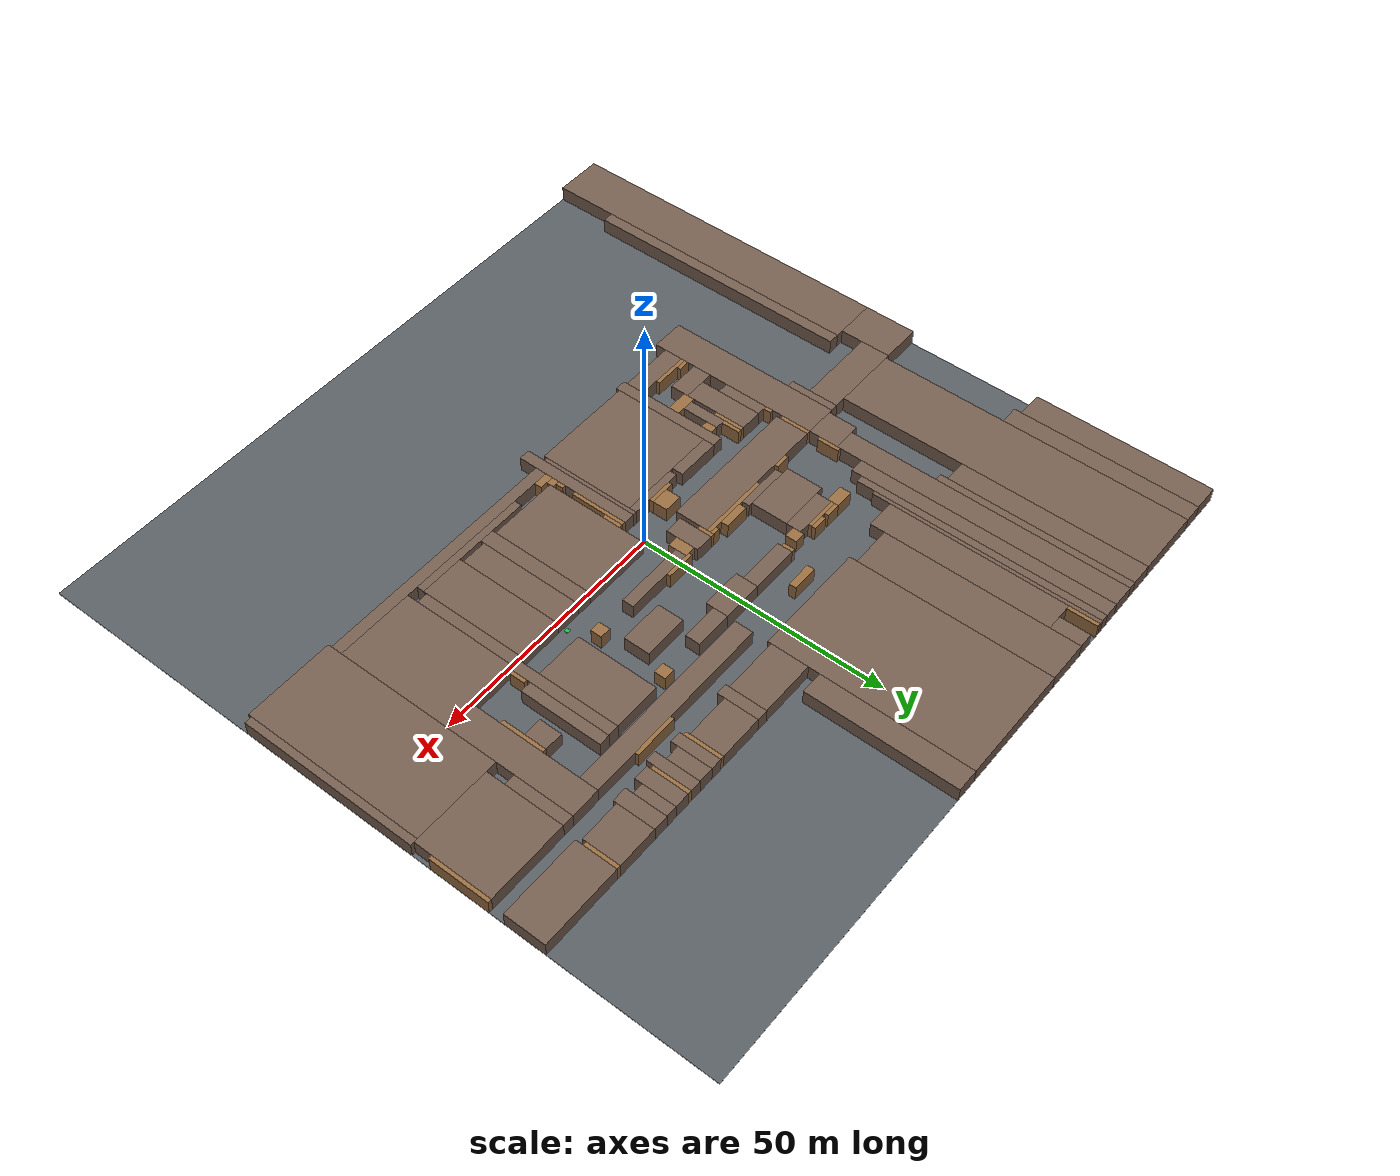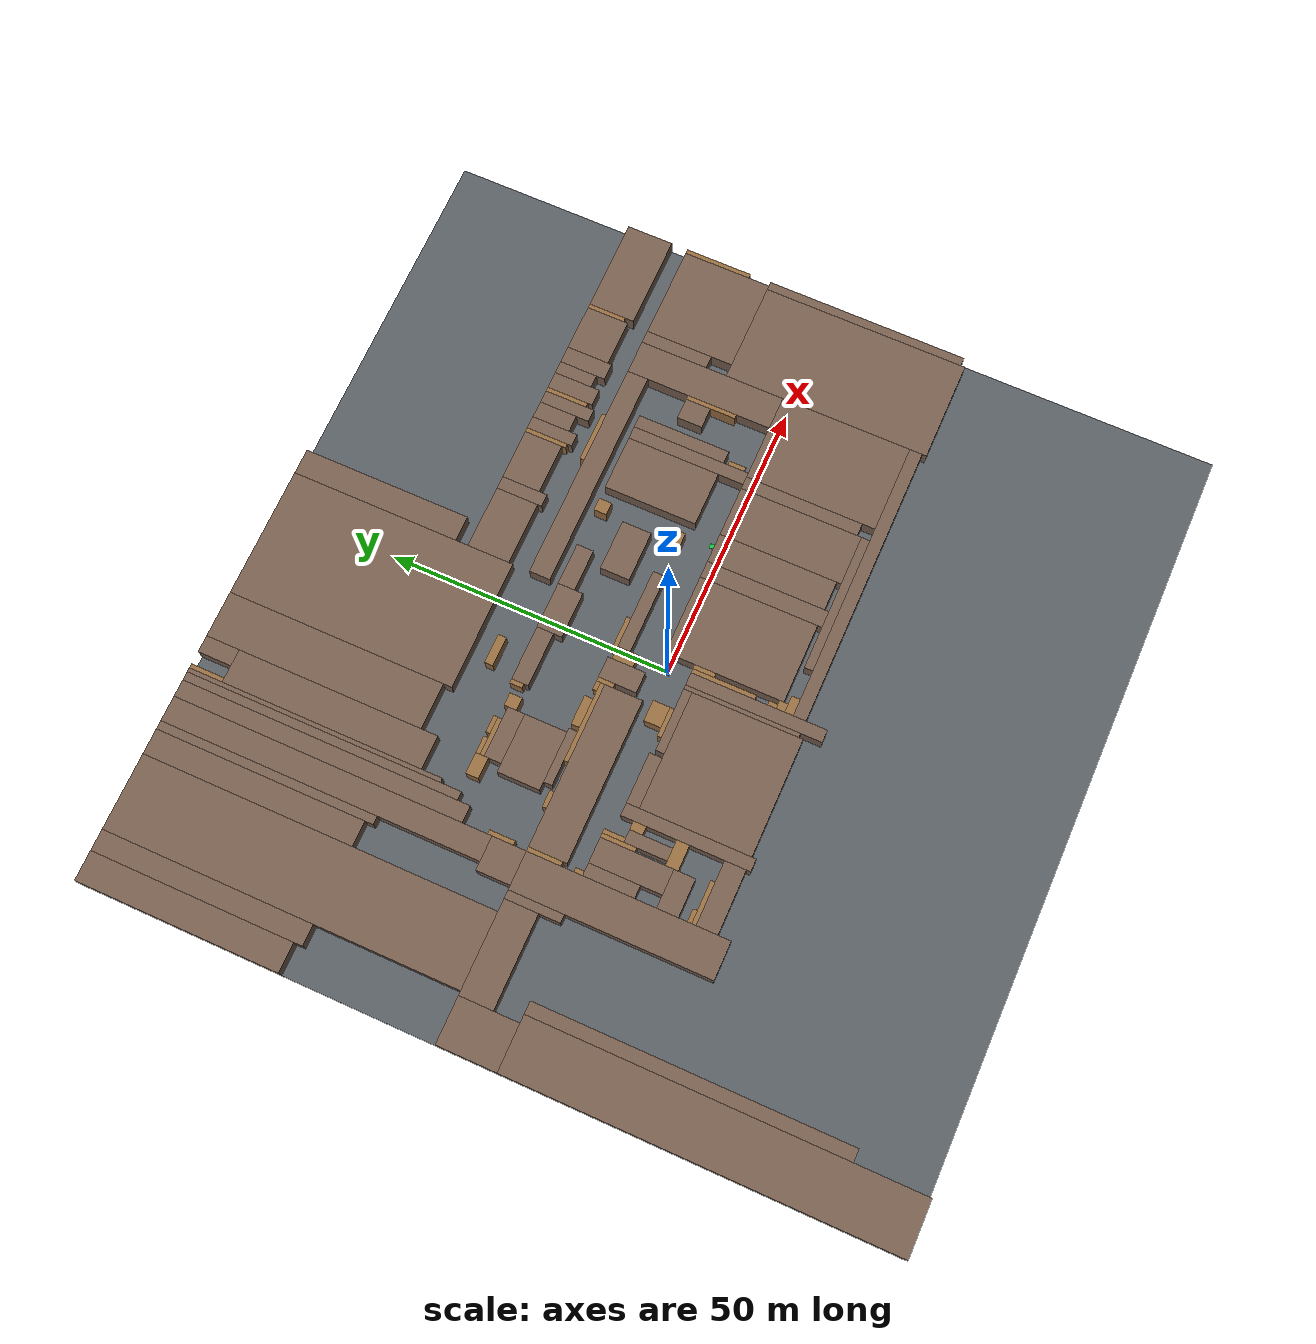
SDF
<?xml version="1.0" ?>
<sdf version="1.9">
  <world name="mosim_ue_factoryenvironmentcollect">
    <physics name="default_physics" type="ignored">
      <max_step_size>0.001</max_step_size>
      <real_time_factor>1.0</real_time_factor>
      <real_time_update_rate>1000</real_time_update_rate>
    </physics>
    <plugin filename="ignition-gazebo-physics-system" name="ignition::gazebo::systems::Physics" />
    <plugin filename="ignition-gazebo-user-commands-system" name="ignition::gazebo::systems::UserCommands" />
    <plugin filename="ignition-gazebo-scene-broadcaster-system" name="ignition::gazebo::systems::SceneBroadcaster" />
    <plugin filename="ignition-gazebo-sensors-system" name="ignition::gazebo::systems::Sensors">
      <render_engine>ogre</render_engine>
    </plugin>
    <plugin filename="ignition-gazebo-imu-system" name="ignition::gazebo::systems::Imu" />
    <light name="sun" type="directional">
      <cast_shadows>true</cast_shadows>
      <pose>0 0 30 0 0 0</pose>
      <diffuse>0.8 0.8 0.8 1</diffuse>
      <specular>0.2 0.2 0.2 1</specular>
      <attenuation>
        <range>1000</range>
        <constant>0.9</constant>
        <linear>0.01</linear>
        <quadratic>0.001</quadratic>
      </attenuation>
      <direction>-0.5 0.1 -0.9</direction>
    </light>
    <model name="ue_truth_ground">
      <static>true</static>
      <pose>0.75 0.75 -0.025 0 0 0</pose>
      <link name="link">
        <collision name="collision">
          <geometry>
            <box>
              <size>141 141 0.05</size>
            </box>
          </geometry>
        </collision>
        <visual name="visual">
          <geometry>
            <box>
              <size>141 141 0.05</size>
            </box>
          </geometry>
          <material>
            <ambient>0.34 0.36 0.38 1</ambient>
            <diffuse>0.34 0.36 0.38 1</diffuse>
          </material>
        </visual>
      </link>
    </model>
    <model name="ue_occ_0000">
      <static>true</static>
      <pose>-64.875 -36 1.5 0 0 0</pose>
      <link name="link">
        <collision name="collision">
          <geometry>
            <box>
              <size>9.75 67.5 3</size>
            </box>
          </geometry>
        </collision>
        <visual name="visual">
          <geometry>
            <box>
              <size>9.75 67.5 3</size>
            </box>
          </geometry>
          <material>
            <ambient>0.45 0.36 0.3 1</ambient>
            <diffuse>0.45 0.36 0.3 1</diffuse>
          </material>
        </visual>
      </link>
    </model>
    <model name="ue_occ_0001">
      <static>true</static>
      <pose>-58.875 -29.625 1.5 0 0 0</pose>
      <link name="link">
        <collision name="collision">
          <geometry>
            <box>
              <size>2.25 54.75 3</size>
            </box>
          </geometry>
        </collision>
        <visual name="visual">
          <geometry>
            <box>
              <size>2.25 54.75 3</size>
            </box>
          </geometry>
          <material>
            <ambient>0.45 0.36 0.3 1</ambient>
            <diffuse>0.45 0.36 0.3 1</diffuse>
          </material>
        </visual>
      </link>
    </model>
    <model name="ue_occ_0002">
      <static>true</static>
      <pose>-0.375 -15.75 1.5 0 0 0</pose>
      <link name="link">
        <collision name="collision">
          <geometry>
            <box>
              <size>2.25 24 3</size>
            </box>
          </geometry>
        </collision>
        <visual name="visual">
          <geometry>
            <box>
              <size>2.25 24 3</size>
            </box>
          </geometry>
          <material>
            <ambient>0.45 0.36 0.3 1</ambient>
            <diffuse>0.45 0.36 0.3 1</diffuse>
          </material>
        </visual>
      </link>
    </model>
    <model name="ue_occ_0003">
      <static>true</static>
      <pose>-40.125 -9.375 1.5 0 0 0</pose>
      <link name="link">
        <collision name="collision">
          <geometry>
            <box>
              <size>6.75 35.25 3</size>
            </box>
          </geometry>
        </collision>
        <visual name="visual">
          <geometry>
            <box>
              <size>6.75 35.25 3</size>
            </box>
          </geometry>
          <material>
            <ambient>0.45 0.36 0.3 1</ambient>
            <diffuse>0.45 0.36 0.3 1</diffuse>
          </material>
        </visual>
      </link>
    </model>
    <model name="ue_occ_0004">
      <static>true</static>
      <pose>-24.375 -14.25 1.5 0 0 0</pose>
      <link name="link">
        <collision name="collision">
          <geometry>
            <box>
              <size>2.25 22.5 3</size>
            </box>
          </geometry>
        </collision>
        <visual name="visual">
          <geometry>
            <box>
              <size>2.25 22.5 3</size>
            </box>
          </geometry>
          <material>
            <ambient>0.45 0.36 0.3 1</ambient>
            <diffuse>0.45 0.36 0.3 1</diffuse>
          </material>
        </visual>
      </link>
    </model>
    <model name="ue_occ_0005">
      <static>true</static>
      <pose>-31.125 -22.875 1.5 0 0 0</pose>
      <link name="link">
        <collision name="collision">
          <geometry>
            <box>
              <size>11.25 3.75 3</size>
            </box>
          </geometry>
        </collision>
        <visual name="visual">
          <geometry>
            <box>
              <size>11.25 3.75 3</size>
            </box>
          </geometry>
          <material>
            <ambient>0.45 0.36 0.3 1</ambient>
            <diffuse>0.45 0.36 0.3 1</diffuse>
          </material>
        </visual>
      </link>
    </model>
    <model name="ue_occ_0006">
      <static>true</static>
      <pose>-12.75 -15 1.5 0 0 0</pose>
      <link name="link">
        <collision name="collision">
          <geometry>
            <box>
              <size>21 19.5 3</size>
            </box>
          </geometry>
        </collision>
        <visual name="visual">
          <geometry>
            <box>
              <size>21 19.5 3</size>
            </box>
          </geometry>
          <material>
            <ambient>0.45 0.36 0.3 1</ambient>
            <diffuse>0.45 0.36 0.3 1</diffuse>
          </material>
        </visual>
      </link>
    </model>
    <model name="ue_occ_0007">
      <static>true</static>
      <pose>60.75 -6.375 1.5 0 0 0</pose>
      <link name="link">
        <collision name="collision">
          <geometry>
            <box>
              <size>18 36.75 3</size>
            </box>
          </geometry>
        </collision>
        <visual name="visual">
          <geometry>
            <box>
              <size>18 36.75 3</size>
            </box>
          </geometry>
          <material>
            <ambient>0.45 0.36 0.3 1</ambient>
            <diffuse>0.45 0.36 0.3 1</diffuse>
          </material>
        </visual>
      </link>
    </model>
    <model name="ue_occ_0008">
      <static>true</static>
      <pose>-1.875 -13.875 1.5 0 0 0</pose>
      <link name="link">
        <collision name="collision">
          <geometry>
            <box>
              <size>0.75 20.25 3</size>
            </box>
          </geometry>
        </collision>
        <visual name="visual">
          <geometry>
            <box>
              <size>0.75 20.25 3</size>
            </box>
          </geometry>
          <material>
            <ambient>0.45 0.36 0.3 1</ambient>
            <diffuse>0.45 0.36 0.3 1</diffuse>
          </material>
        </visual>
      </link>
    </model>
    <model name="ue_occ_0009">
      <static>true</static>
      <pose>26.25 -22.875 1.5 0 0 0</pose>
      <link name="link">
        <collision name="collision">
          <geometry>
            <box>
              <size>51 2.25 3</size>
            </box>
          </geometry>
        </collision>
        <visual name="visual">
          <geometry>
            <box>
              <size>51 2.25 3</size>
            </box>
          </geometry>
          <material>
            <ambient>0.45 0.36 0.3 1</ambient>
            <diffuse>0.45 0.36 0.3 1</diffuse>
          </material>
        </visual>
      </link>
    </model>
    <model name="ue_occ_0010">
      <static>true</static>
      <pose>70.5 -6 1.5 0 0 0</pose>
      <link name="link">
        <collision name="collision">
          <geometry>
            <box>
              <size>1.5 36 3</size>
            </box>
          </geometry>
        </collision>
        <visual name="visual">
          <geometry>
            <box>
              <size>1.5 36 3</size>
            </box>
          </geometry>
          <material>
            <ambient>0.45 0.36 0.3 1</ambient>
            <diffuse>0.45 0.36 0.3 1</diffuse>
          </material>
        </visual>
      </link>
    </model>
    <model name="ue_occ_0011">
      <static>true</static>
      <pose>2.25 -21 1.5 0 0 0</pose>
      <link name="link">
        <collision name="collision">
          <geometry>
            <box>
              <size>3 1.5 3</size>
            </box>
          </geometry>
        </collision>
        <visual name="visual">
          <geometry>
            <box>
              <size>3 1.5 3</size>
            </box>
          </geometry>
          <material>
            <ambient>0.58 0.42 0.25 1</ambient>
            <diffuse>0.58 0.42 0.25 1</diffuse>
          </material>
        </visual>
      </link>
    </model>
    <model name="ue_occ_0012">
      <static>true</static>
      <pose>21.375 -21 1.5 0 0 0</pose>
      <link name="link">
        <collision name="collision">
          <geometry>
            <box>
              <size>24.75 1.5 3</size>
            </box>
          </geometry>
        </collision>
        <visual name="visual">
          <geometry>
            <box>
              <size>24.75 1.5 3</size>
            </box>
          </geometry>
          <material>
            <ambient>0.45 0.36 0.3 1</ambient>
            <diffuse>0.45 0.36 0.3 1</diffuse>
          </material>
        </visual>
      </link>
    </model>
    <model name="ue_occ_0013">
      <static>true</static>
      <pose>43.875 -10.125 1.5 0 0 0</pose>
      <link name="link">
        <collision name="collision">
          <geometry>
            <box>
              <size>15.75 23.25 3</size>
            </box>
          </geometry>
        </collision>
        <visual name="visual">
          <geometry>
            <box>
              <size>15.75 23.25 3</size>
            </box>
          </geometry>
          <material>
            <ambient>0.45 0.36 0.3 1</ambient>
            <diffuse>0.45 0.36 0.3 1</diffuse>
          </material>
        </visual>
      </link>
    </model>
    <model name="ue_occ_0014">
      <static>true</static>
      <pose>-33 -20.625 1.5 0 0 0</pose>
      <link name="link">
        <collision name="collision">
          <geometry>
            <box>
              <size>7.5 0.75 3</size>
            </box>
          </geometry>
        </collision>
        <visual name="visual">
          <geometry>
            <box>
              <size>7.5 0.75 3</size>
            </box>
          </geometry>
          <material>
            <ambient>0.58 0.42 0.25 1</ambient>
            <diffuse>0.58 0.42 0.25 1</diffuse>
          </material>
        </visual>
      </link>
    </model>
    <model name="ue_occ_0015">
      <static>true</static>
      <pose>-35.625 -19.875 1.5 0 0 0</pose>
      <link name="link">
        <collision name="collision">
          <geometry>
            <box>
              <size>2.25 0.75 3</size>
            </box>
          </geometry>
        </collision>
        <visual name="visual">
          <geometry>
            <box>
              <size>2.25 0.75 3</size>
            </box>
          </geometry>
          <material>
            <ambient>0.58 0.42 0.25 1</ambient>
            <diffuse>0.58 0.42 0.25 1</diffuse>
          </material>
        </visual>
      </link>
    </model>
    <model name="ue_occ_0016">
      <static>true</static>
      <pose>1.5 -19.5 1.5 0 0 0</pose>
      <link name="link">
        <collision name="collision">
          <geometry>
            <box>
              <size>1.5 1.5 3</size>
            </box>
          </geometry>
        </collision>
        <visual name="visual">
          <geometry>
            <box>
              <size>1.5 1.5 3</size>
            </box>
          </geometry>
          <material>
            <ambient>0.58 0.42 0.25 1</ambient>
            <diffuse>0.58 0.42 0.25 1</diffuse>
          </material>
        </visual>
      </link>
    </model>
    <model name="ue_occ_0017">
      <static>true</static>
      <pose>18 -9.375 1.5 0 0 0</pose>
      <link name="link">
        <collision name="collision">
          <geometry>
            <box>
              <size>3 21.75 3</size>
            </box>
          </geometry>
        </collision>
        <visual name="visual">
          <geometry>
            <box>
              <size>3 21.75 3</size>
            </box>
          </geometry>
          <material>
            <ambient>0.45 0.36 0.3 1</ambient>
            <diffuse>0.45 0.36 0.3 1</diffuse>
          </material>
        </visual>
      </link>
    </model>
    <model name="ue_occ_0018">
      <static>true</static>
      <pose>29.25 -9.375 1.5 0 0 0</pose>
      <link name="link">
        <collision name="collision">
          <geometry>
            <box>
              <size>9 21.75 3</size>
            </box>
          </geometry>
        </collision>
        <visual name="visual">
          <geometry>
            <box>
              <size>9 21.75 3</size>
            </box>
          </geometry>
          <material>
            <ambient>0.45 0.36 0.3 1</ambient>
            <diffuse>0.45 0.36 0.3 1</diffuse>
          </material>
        </visual>
      </link>
    </model>
    <model name="ue_occ_0019">
      <static>true</static>
      <pose>9.375 -9 1.5 0 0 0</pose>
      <link name="link">
        <collision name="collision">
          <geometry>
            <box>
              <size>14.25 21 3</size>
            </box>
          </geometry>
        </collision>
        <visual name="visual">
          <geometry>
            <box>
              <size>14.25 21 3</size>
            </box>
          </geometry>
          <material>
            <ambient>0.45 0.36 0.3 1</ambient>
            <diffuse>0.45 0.36 0.3 1</diffuse>
          </material>
        </visual>
      </link>
    </model>
    <model name="ue_occ_0020">
      <static>true</static>
      <pose>22.125 -9 1.5 0 0 0</pose>
      <link name="link">
        <collision name="collision">
          <geometry>
            <box>
              <size>5.25 21 3</size>
            </box>
          </geometry>
        </collision>
        <visual name="visual">
          <geometry>
            <box>
              <size>5.25 21 3</size>
            </box>
          </geometry>
          <material>
            <ambient>0.45 0.36 0.3 1</ambient>
            <diffuse>0.45 0.36 0.3 1</diffuse>
          </material>
        </visual>
      </link>
    </model>
    <model name="ue_occ_0021">
      <static>true</static>
      <pose>34.875 -9 1.5 0 0 0</pose>
      <link name="link">
        <collision name="collision">
          <geometry>
            <box>
              <size>2.25 21 3</size>
            </box>
          </geometry>
        </collision>
        <visual name="visual">
          <geometry>
            <box>
              <size>2.25 21 3</size>
            </box>
          </geometry>
          <material>
            <ambient>0.45 0.36 0.3 1</ambient>
            <diffuse>0.45 0.36 0.3 1</diffuse>
          </material>
        </visual>
      </link>
    </model>
    <model name="ue_occ_0022">
      <static>true</static>
      <pose>1.125 -18 1.5 0 0 0</pose>
      <link name="link">
        <collision name="collision">
          <geometry>
            <box>
              <size>0.75 1.5 3</size>
            </box>
          </geometry>
        </collision>
        <visual name="visual">
          <geometry>
            <box>
              <size>0.75 1.5 3</size>
            </box>
          </geometry>
          <material>
            <ambient>0.58 0.42 0.25 1</ambient>
            <diffuse>0.58 0.42 0.25 1</diffuse>
          </material>
        </visual>
      </link>
    </model>
    <model name="ue_occ_0023">
      <static>true</static>
      <pose>-33.375 -16.125 1.5 0 0 0</pose>
      <link name="link">
        <collision name="collision">
          <geometry>
            <box>
              <size>6.75 3.75 3</size>
            </box>
          </geometry>
        </collision>
        <visual name="visual">
          <geometry>
            <box>
              <size>6.75 3.75 3</size>
            </box>
          </geometry>
          <material>
            <ambient>0.45 0.36 0.3 1</ambient>
            <diffuse>0.45 0.36 0.3 1</diffuse>
          </material>
        </visual>
      </link>
    </model>
    <model name="ue_occ_0024">
      <static>true</static>
      <pose>-27.75 -13.875 1.5 0 0 0</pose>
      <link name="link">
        <collision name="collision">
          <geometry>
            <box>
              <size>4.5 2.25 3</size>
            </box>
          </geometry>
        </collision>
        <visual name="visual">
          <geometry>
            <box>
              <size>4.5 2.25 3</size>
            </box>
          </geometry>
          <material>
            <ambient>0.58 0.42 0.25 1</ambient>
            <diffuse>0.58 0.42 0.25 1</diffuse>
          </material>
        </visual>
      </link>
    </model>
    <model name="ue_occ_0025">
      <static>true</static>
      <pose>1.125 -9.375 1.5 0 0 0</pose>
      <link name="link">
        <collision name="collision">
          <geometry>
            <box>
              <size>0.75 11.25 3</size>
            </box>
          </geometry>
        </collision>
        <visual name="visual">
          <geometry>
            <box>
              <size>0.75 11.25 3</size>
            </box>
          </geometry>
          <material>
            <ambient>0.58 0.42 0.25 1</ambient>
            <diffuse>0.58 0.42 0.25 1</diffuse>
          </material>
        </visual>
      </link>
    </model>
    <model name="ue_occ_0026">
      <static>true</static>
      <pose>-32.25 -7.875 1.5 0 0 0</pose>
      <link name="link">
        <collision name="collision">
          <geometry>
            <box>
              <size>4.5 12.75 3</size>
            </box>
          </geometry>
        </collision>
        <visual name="visual">
          <geometry>
            <box>
              <size>4.5 12.75 3</size>
            </box>
          </geometry>
          <material>
            <ambient>0.45 0.36 0.3 1</ambient>
            <diffuse>0.45 0.36 0.3 1</diffuse>
          </material>
        </visual>
      </link>
    </model>
    <model name="ue_occ_0027">
      <static>true</static>
      <pose>-28.125 -9 1.5 0 0 0</pose>
      <link name="link">
        <collision name="collision">
          <geometry>
            <box>
              <size>2.25 7.5 3</size>
            </box>
          </geometry>
        </collision>
        <visual name="visual">
          <geometry>
            <box>
              <size>2.25 7.5 3</size>
            </box>
          </geometry>
          <material>
            <ambient>0.45 0.36 0.3 1</ambient>
            <diffuse>0.45 0.36 0.3 1</diffuse>
          </material>
        </visual>
      </link>
    </model>
    <model name="ue_occ_0028">
      <static>true</static>
      <pose>-35.625 -6 1.5 0 0 0</pose>
      <link name="link">
        <collision name="collision">
          <geometry>
            <box>
              <size>2.25 9 3</size>
            </box>
          </geometry>
        </collision>
        <visual name="visual">
          <geometry>
            <box>
              <size>2.25 9 3</size>
            </box>
          </geometry>
          <material>
            <ambient>0.45 0.36 0.3 1</ambient>
            <diffuse>0.45 0.36 0.3 1</diffuse>
          </material>
        </visual>
      </link>
    </model>
    <model name="ue_occ_0029">
      <static>true</static>
      <pose>-29.625 -4.5 1.5 0 0 0</pose>
      <link name="link">
        <collision name="collision">
          <geometry>
            <box>
              <size>0.75 6 3</size>
            </box>
          </geometry>
        </collision>
        <visual name="visual">
          <geometry>
            <box>
              <size>0.75 6 3</size>
            </box>
          </geometry>
          <material>
            <ambient>0.58 0.42 0.25 1</ambient>
            <diffuse>0.58 0.42 0.25 1</diffuse>
          </material>
        </visual>
      </link>
    </model>
    <model name="ue_occ_0030">
      <static>true</static>
      <pose>-26.25 -6.375 1.5 0 0 0</pose>
      <link name="link">
        <collision name="collision">
          <geometry>
            <box>
              <size>1.5 2.25 3</size>
            </box>
          </geometry>
        </collision>
        <visual name="visual">
          <geometry>
            <box>
              <size>1.5 2.25 3</size>
            </box>
          </geometry>
          <material>
            <ambient>0.58 0.42 0.25 1</ambient>
            <diffuse>0.58 0.42 0.25 1</diffuse>
          </material>
        </visual>
      </link>
    </model>
    <model name="ue_occ_0031">
      <static>true</static>
      <pose>1.875 -5.625 1.5 0 0 0</pose>
      <link name="link">
        <collision name="collision">
          <geometry>
            <box>
              <size>0.75 3.75 3</size>
            </box>
          </geometry>
        </collision>
        <visual name="visual">
          <geometry>
            <box>
              <size>0.75 3.75 3</size>
            </box>
          </geometry>
          <material>
            <ambient>0.58 0.42 0.25 1</ambient>
            <diffuse>0.58 0.42 0.25 1</diffuse>
          </material>
        </visual>
      </link>
    </model>
    <model name="ue_occ_0032">
      <static>true</static>
      <pose>-28.875 -3.375 1.5 0 0 0</pose>
      <link name="link">
        <collision name="collision">
          <geometry>
            <box>
              <size>0.75 3.75 3</size>
            </box>
          </geometry>
        </collision>
        <visual name="visual">
          <geometry>
            <box>
              <size>0.75 3.75 3</size>
            </box>
          </geometry>
          <material>
            <ambient>0.58 0.42 0.25 1</ambient>
            <diffuse>0.58 0.42 0.25 1</diffuse>
          </material>
        </visual>
      </link>
    </model>
    <model name="ue_occ_0033">
      <static>true</static>
      <pose>-18.75 -4.125 1.5 0 0 0</pose>
      <link name="link">
        <collision name="collision">
          <geometry>
            <box>
              <size>9 2.25 3</size>
            </box>
          </geometry>
        </collision>
        <visual name="visual">
          <geometry>
            <box>
              <size>9 2.25 3</size>
            </box>
          </geometry>
          <material>
            <ambient>0.45 0.36 0.3 1</ambient>
            <diffuse>0.45 0.36 0.3 1</diffuse>
          </material>
        </visual>
      </link>
    </model>
    <model name="ue_occ_0034">
      <static>true</static>
      <pose>-7.875 -4.5 1.5 0 0 0</pose>
      <link name="link">
        <collision name="collision">
          <geometry>
            <box>
              <size>11.25 1.5 3</size>
            </box>
          </geometry>
        </collision>
        <visual name="visual">
          <geometry>
            <box>
              <size>11.25 1.5 3</size>
            </box>
          </geometry>
          <material>
            <ambient>0.45 0.36 0.3 1</ambient>
            <diffuse>0.45 0.36 0.3 1</diffuse>
          </material>
        </visual>
      </link>
    </model>
    <model name="ue_occ_0035">
      <static>true</static>
      <pose>-8.625 -3.375 1.5 0 0 0</pose>
      <link name="link">
        <collision name="collision">
          <geometry>
            <box>
              <size>5.25 0.75 3</size>
            </box>
          </geometry>
        </collision>
        <visual name="visual">
          <geometry>
            <box>
              <size>5.25 0.75 3</size>
            </box>
          </geometry>
          <material>
            <ambient>0.58 0.42 0.25 1</ambient>
            <diffuse>0.58 0.42 0.25 1</diffuse>
          </material>
        </visual>
      </link>
    </model>
    <model name="ue_occ_0036">
      <static>true</static>
      <pose>-7.875 -1.5 1.5 0 0 0</pose>
      <link name="link">
        <collision name="collision">
          <geometry>
            <box>
              <size>3.75 3 3</size>
            </box>
          </geometry>
        </collision>
        <visual name="visual">
          <geometry>
            <box>
              <size>3.75 3 3</size>
            </box>
          </geometry>
          <material>
            <ambient>0.58 0.42 0.25 1</ambient>
            <diffuse>0.58 0.42 0.25 1</diffuse>
          </material>
        </visual>
      </link>
    </model>
    <model name="ue_occ_0037">
      <static>true</static>
      <pose>-65.625 3 1.5 0 0 0</pose>
      <link name="link">
        <collision name="collision">
          <geometry>
            <box>
              <size>8.25 10.5 3</size>
            </box>
          </geometry>
        </collision>
        <visual name="visual">
          <geometry>
            <box>
              <size>8.25 10.5 3</size>
            </box>
          </geometry>
          <material>
            <ambient>0.45 0.36 0.3 1</ambient>
            <diffuse>0.45 0.36 0.3 1</diffuse>
          </material>
        </visual>
      </link>
    </model>
    <model name="ue_occ_0038">
      <static>true</static>
      <pose>-44.25 3.375 1.5 0 0 0</pose>
      <link name="link">
        <collision name="collision">
          <geometry>
            <box>
              <size>1.5 9.75 3</size>
            </box>
          </geometry>
        </collision>
        <visual name="visual">
          <geometry>
            <box>
              <size>1.5 9.75 3</size>
            </box>
          </geometry>
          <material>
            <ambient>0.45 0.36 0.3 1</ambient>
            <diffuse>0.45 0.36 0.3 1</diffuse>
          </material>
        </visual>
      </link>
    </model>
    <model name="ue_occ_0039">
      <static>true</static>
      <pose>-36.375 -0.75 1.5 0 0 0</pose>
      <link name="link">
        <collision name="collision">
          <geometry>
            <box>
              <size>0.75 1.5 3</size>
            </box>
          </geometry>
        </collision>
        <visual name="visual">
          <geometry>
            <box>
              <size>0.75 1.5 3</size>
            </box>
          </geometry>
          <material>
            <ambient>0.58 0.42 0.25 1</ambient>
            <diffuse>0.58 0.42 0.25 1</diffuse>
          </material>
        </visual>
      </link>
    </model>
    <model name="ue_occ_0040">
      <static>true</static>
      <pose>-21.375 4.875 1.5 0 0 0</pose>
      <link name="link">
        <collision name="collision">
          <geometry>
            <box>
              <size>29.25 6.75 3</size>
            </box>
          </geometry>
        </collision>
        <visual name="visual">
          <geometry>
            <box>
              <size>29.25 6.75 3</size>
            </box>
          </geometry>
          <material>
            <ambient>0.45 0.36 0.3 1</ambient>
            <diffuse>0.45 0.36 0.3 1</diffuse>
          </material>
        </visual>
      </link>
    </model>
    <model name="ue_occ_0041">
      <static>true</static>
      <pose>35.625 12 1.5 0 0 0</pose>
      <link name="link">
        <collision name="collision">
          <geometry>
            <box>
              <size>2.25 21 3</size>
            </box>
          </geometry>
        </collision>
        <visual name="visual">
          <geometry>
            <box>
              <size>2.25 21 3</size>
            </box>
          </geometry>
          <material>
            <ambient>0.45 0.36 0.3 1</ambient>
            <diffuse>0.45 0.36 0.3 1</diffuse>
          </material>
        </visual>
      </link>
    </model>
    <model name="ue_occ_0042">
      <static>true</static>
      <pose>48.75 14.625 1.5 0 0 0</pose>
      <link name="link">
        <collision name="collision">
          <geometry>
            <box>
              <size>6 26.25 3</size>
            </box>
          </geometry>
        </collision>
        <visual name="visual">
          <geometry>
            <box>
              <size>6 26.25 3</size>
            </box>
          </geometry>
          <material>
            <ambient>0.45 0.36 0.3 1</ambient>
            <diffuse>0.45 0.36 0.3 1</diffuse>
          </material>
        </visual>
      </link>
    </model>
    <model name="ue_occ_0043">
      <static>true</static>
      <pose>-53.25 5.25 1.5 0 0 0</pose>
      <link name="link">
        <collision name="collision">
          <geometry>
            <box>
              <size>16.5 6 3</size>
            </box>
          </geometry>
        </collision>
        <visual name="visual">
          <geometry>
            <box>
              <size>16.5 6 3</size>
            </box>
          </geometry>
          <material>
            <ambient>0.45 0.36 0.3 1</ambient>
            <diffuse>0.45 0.36 0.3 1</diffuse>
          </material>
        </visual>
      </link>
    </model>
    <model name="ue_occ_0044">
      <static>true</static>
      <pose>-36.375 5.25 1.5 0 0 0</pose>
      <link name="link">
        <collision name="collision">
          <geometry>
            <box>
              <size>0.75 6 3</size>
            </box>
          </geometry>
        </collision>
        <visual name="visual">
          <geometry>
            <box>
              <size>0.75 6 3</size>
            </box>
          </geometry>
          <material>
            <ambient>0.58 0.42 0.25 1</ambient>
            <diffuse>0.58 0.42 0.25 1</diffuse>
          </material>
        </visual>
      </link>
    </model>
    <model name="ue_occ_0045">
      <static>true</static>
      <pose>37.125 3.75 1.5 0 0 0</pose>
      <link name="link">
        <collision name="collision">
          <geometry>
            <box>
              <size>0.75 3 3</size>
            </box>
          </geometry>
        </collision>
        <visual name="visual">
          <geometry>
            <box>
              <size>0.75 3 3</size>
            </box>
          </geometry>
          <material>
            <ambient>0.58 0.42 0.25 1</ambient>
            <diffuse>0.58 0.42 0.25 1</diffuse>
          </material>
        </visual>
      </link>
    </model>
    <model name="ue_occ_0046">
      <static>true</static>
      <pose>-4.125 6.375 1.5 0 0 0</pose>
      <link name="link">
        <collision name="collision">
          <geometry>
            <box>
              <size>3.75 6.75 3</size>
            </box>
          </geometry>
        </collision>
        <visual name="visual">
          <geometry>
            <box>
              <size>3.75 6.75 3</size>
            </box>
          </geometry>
          <material>
            <ambient>0.45 0.36 0.3 1</ambient>
            <diffuse>0.45 0.36 0.3 1</diffuse>
          </material>
        </visual>
      </link>
    </model>
    <model name="ue_occ_0047">
      <static>true</static>
      <pose>-1.125 7.125 1.5 0 0 0</pose>
      <link name="link">
        <collision name="collision">
          <geometry>
            <box>
              <size>2.25 3.75 3</size>
            </box>
          </geometry>
        </collision>
        <visual name="visual">
          <geometry>
            <box>
              <size>2.25 3.75 3</size>
            </box>
          </geometry>
          <material>
            <ambient>0.58 0.42 0.25 1</ambient>
            <diffuse>0.58 0.42 0.25 1</diffuse>
          </material>
        </visual>
      </link>
    </model>
    <model name="ue_occ_0048">
      <static>true</static>
      <pose>29.625 14.25 1.5 0 0 0</pose>
      <link name="link">
        <collision name="collision">
          <geometry>
            <box>
              <size>9.75 16.5 3</size>
            </box>
          </geometry>
        </collision>
        <visual name="visual">
          <geometry>
            <box>
              <size>9.75 16.5 3</size>
            </box>
          </geometry>
          <material>
            <ambient>0.45 0.36 0.3 1</ambient>
            <diffuse>0.45 0.36 0.3 1</diffuse>
          </material>
        </visual>
      </link>
    </model>
    <model name="ue_occ_0049">
      <static>true</static>
      <pose>37.875 14.25 1.5 0 0 0</pose>
      <link name="link">
        <collision name="collision">
          <geometry>
            <box>
              <size>2.25 16.5 3</size>
            </box>
          </geometry>
        </collision>
        <visual name="visual">
          <geometry>
            <box>
              <size>2.25 16.5 3</size>
            </box>
          </geometry>
          <material>
            <ambient>0.45 0.36 0.3 1</ambient>
            <diffuse>0.45 0.36 0.3 1</diffuse>
          </material>
        </visual>
      </link>
    </model>
    <model name="ue_occ_0050">
      <static>true</static>
      <pose>-6.375 8.25 1.5 0 0 0</pose>
      <link name="link">
        <collision name="collision">
          <geometry>
            <box>
              <size>0.75 3 3</size>
            </box>
          </geometry>
        </collision>
        <visual name="visual">
          <geometry>
            <box>
              <size>0.75 3 3</size>
            </box>
          </geometry>
          <material>
            <ambient>0.58 0.42 0.25 1</ambient>
            <diffuse>0.58 0.42 0.25 1</diffuse>
          </material>
        </visual>
      </link>
    </model>
    <model name="ue_occ_0051">
      <static>true</static>
      <pose>7.125 7.875 1.5 0 0 0</pose>
      <link name="link">
        <collision name="collision">
          <geometry>
            <box>
              <size>14.25 2.25 3</size>
            </box>
          </geometry>
        </collision>
        <visual name="visual">
          <geometry>
            <box>
              <size>14.25 2.25 3</size>
            </box>
          </geometry>
          <material>
            <ambient>0.45 0.36 0.3 1</ambient>
            <diffuse>0.45 0.36 0.3 1</diffuse>
          </material>
        </visual>
      </link>
    </model>
    <model name="ue_occ_0052">
      <static>true</static>
      <pose>21.375 7.875 1.5 0 0 0</pose>
      <link name="link">
        <collision name="collision">
          <geometry>
            <box>
              <size>2.25 2.25 3</size>
            </box>
          </geometry>
        </collision>
        <visual name="visual">
          <geometry>
            <box>
              <size>2.25 2.25 3</size>
            </box>
          </geometry>
          <material>
            <ambient>0.58 0.42 0.25 1</ambient>
            <diffuse>0.58 0.42 0.25 1</diffuse>
          </material>
        </visual>
      </link>
    </model>
    <model name="ue_occ_0053">
      <static>true</static>
      <pose>45.375 12 1.5 0 0 0</pose>
      <link name="link">
        <collision name="collision">
          <geometry>
            <box>
              <size>0.75 9 3</size>
            </box>
          </geometry>
        </collision>
        <visual name="visual">
          <geometry>
            <box>
              <size>0.75 9 3</size>
            </box>
          </geometry>
          <material>
            <ambient>0.58 0.42 0.25 1</ambient>
            <diffuse>0.58 0.42 0.25 1</diffuse>
          </material>
        </visual>
      </link>
    </model>
    <model name="ue_occ_0054">
      <static>true</static>
      <pose>-54 39.75 1.5 0 0 0</pose>
      <link name="link">
        <collision name="collision">
          <geometry>
            <box>
              <size>13.5 63 3</size>
            </box>
          </geometry>
        </collision>
        <visual name="visual">
          <geometry>
            <box>
              <size>13.5 63 3</size>
            </box>
          </geometry>
          <material>
            <ambient>0.45 0.36 0.3 1</ambient>
            <diffuse>0.45 0.36 0.3 1</diffuse>
          </material>
        </visual>
      </link>
    </model>
    <model name="ue_occ_0055">
      <static>true</static>
      <pose>-39.75 11.25 1.5 0 0 0</pose>
      <link name="link">
        <collision name="collision">
          <geometry>
            <box>
              <size>6 6 3</size>
            </box>
          </geometry>
        </collision>
        <visual name="visual">
          <geometry>
            <box>
              <size>6 6 3</size>
            </box>
          </geometry>
          <material>
            <ambient>0.45 0.36 0.3 1</ambient>
            <diffuse>0.45 0.36 0.3 1</diffuse>
          </material>
        </visual>
      </link>
    </model>
    <model name="ue_occ_0056">
      <static>true</static>
      <pose>-27.75 8.625 1.5 0 0 0</pose>
      <link name="link">
        <collision name="collision">
          <geometry>
            <box>
              <size>3 0.75 3</size>
            </box>
          </geometry>
        </collision>
        <visual name="visual">
          <geometry>
            <box>
              <size>3 0.75 3</size>
            </box>
          </geometry>
          <material>
            <ambient>0.58 0.42 0.25 1</ambient>
            <diffuse>0.58 0.42 0.25 1</diffuse>
          </material>
        </visual>
      </link>
    </model>
    <model name="ue_occ_0057">
      <static>true</static>
      <pose>-13.875 8.625 1.5 0 0 0</pose>
      <link name="link">
        <collision name="collision">
          <geometry>
            <box>
              <size>14.25 0.75 3</size>
            </box>
          </geometry>
        </collision>
        <visual name="visual">
          <geometry>
            <box>
              <size>14.25 0.75 3</size>
            </box>
          </geometry>
          <material>
            <ambient>0.58 0.42 0.25 1</ambient>
            <diffuse>0.58 0.42 0.25 1</diffuse>
          </material>
        </visual>
      </link>
    </model>
    <model name="ue_occ_0058">
      <static>true</static>
      <pose>-20.625 9.75 1.5 0 0 0</pose>
      <link name="link">
        <collision name="collision">
          <geometry>
            <box>
              <size>9.75 1.5 3</size>
            </box>
          </geometry>
        </collision>
        <visual name="visual">
          <geometry>
            <box>
              <size>9.75 1.5 3</size>
            </box>
          </geometry>
          <material>
            <ambient>0.45 0.36 0.3 1</ambient>
            <diffuse>0.45 0.36 0.3 1</diffuse>
          </material>
        </visual>
      </link>
    </model>
    <model name="ue_occ_0059">
      <static>true</static>
      <pose>-12.375 9.75 1.5 0 0 0</pose>
      <link name="link">
        <collision name="collision">
          <geometry>
            <box>
              <size>5.25 1.5 3</size>
            </box>
          </geometry>
        </collision>
        <visual name="visual">
          <geometry>
            <box>
              <size>5.25 1.5 3</size>
            </box>
          </geometry>
          <material>
            <ambient>0.58 0.42 0.25 1</ambient>
            <diffuse>0.58 0.42 0.25 1</diffuse>
          </material>
        </visual>
      </link>
    </model>
    <model name="ue_occ_0060">
      <static>true</static>
      <pose>-7.5 9.375 1.5 0 0 0</pose>
      <link name="link">
        <collision name="collision">
          <geometry>
            <box>
              <size>1.5 0.75 3</size>
            </box>
          </geometry>
        </collision>
        <visual name="visual">
          <geometry>
            <box>
              <size>1.5 0.75 3</size>
            </box>
          </geometry>
          <material>
            <ambient>0.58 0.42 0.25 1</ambient>
            <diffuse>0.58 0.42 0.25 1</diffuse>
          </material>
        </visual>
      </link>
    </model>
    <model name="ue_occ_0061">
      <static>true</static>
      <pose>2.25 9.375 1.5 0 0 0</pose>
      <link name="link">
        <collision name="collision">
          <geometry>
            <box>
              <size>6 0.75 3</size>
            </box>
          </geometry>
        </collision>
        <visual name="visual">
          <geometry>
            <box>
              <size>6 0.75 3</size>
            </box>
          </geometry>
          <material>
            <ambient>0.58 0.42 0.25 1</ambient>
            <diffuse>0.58 0.42 0.25 1</diffuse>
          </material>
        </visual>
      </link>
    </model>
    <model name="ue_occ_0062">
      <static>true</static>
      <pose>-36.375 12.75 1.5 0 0 0</pose>
      <link name="link">
        <collision name="collision">
          <geometry>
            <box>
              <size>0.75 4.5 3</size>
            </box>
          </geometry>
        </collision>
        <visual name="visual">
          <geometry>
            <box>
              <size>0.75 4.5 3</size>
            </box>
          </geometry>
          <material>
            <ambient>0.58 0.42 0.25 1</ambient>
            <diffuse>0.58 0.42 0.25 1</diffuse>
          </material>
        </visual>
      </link>
    </model>
    <model name="ue_occ_0063">
      <static>true</static>
      <pose>-21.75 14.25 1.5 0 0 0</pose>
      <link name="link">
        <collision name="collision">
          <geometry>
            <box>
              <size>10.5 7.5 3</size>
            </box>
          </geometry>
        </collision>
        <visual name="visual">
          <geometry>
            <box>
              <size>10.5 7.5 3</size>
            </box>
          </geometry>
          <material>
            <ambient>0.45 0.36 0.3 1</ambient>
            <diffuse>0.45 0.36 0.3 1</diffuse>
          </material>
        </visual>
      </link>
    </model>
    <model name="ue_occ_0064">
      <static>true</static>
      <pose>15.75 14.625 1.5 0 0 0</pose>
      <link name="link">
        <collision name="collision">
          <geometry>
            <box>
              <size>9 5.25 3</size>
            </box>
          </geometry>
        </collision>
        <visual name="visual">
          <geometry>
            <box>
              <size>9 5.25 3</size>
            </box>
          </geometry>
          <material>
            <ambient>0.45 0.36 0.3 1</ambient>
            <diffuse>0.45 0.36 0.3 1</diffuse>
          </material>
        </visual>
      </link>
    </model>
    <model name="ue_occ_0065">
      <static>true</static>
      <pose>43.125 14.25 1.5 0 0 0</pose>
      <link name="link">
        <collision name="collision">
          <geometry>
            <box>
              <size>3.75 4.5 3</size>
            </box>
          </geometry>
        </collision>
        <visual name="visual">
          <geometry>
            <box>
              <size>3.75 4.5 3</size>
            </box>
          </geometry>
          <material>
            <ambient>0.45 0.36 0.3 1</ambient>
            <diffuse>0.45 0.36 0.3 1</diffuse>
          </material>
        </visual>
      </link>
    </model>
    <model name="ue_occ_0066">
      <static>true</static>
      <pose>62.25 19.875 1.5 0 0 0</pose>
      <link name="link">
        <collision name="collision">
          <geometry>
            <box>
              <size>16.5 15.75 3</size>
            </box>
          </geometry>
        </collision>
        <visual name="visual">
          <geometry>
            <box>
              <size>16.5 15.75 3</size>
            </box>
          </geometry>
          <material>
            <ambient>0.45 0.36 0.3 1</ambient>
            <diffuse>0.45 0.36 0.3 1</diffuse>
          </material>
        </visual>
      </link>
    </model>
    <model name="ue_occ_0067">
      <static>true</static>
      <pose>-39 42.75 1.5 0 0 0</pose>
      <link name="link">
        <collision name="collision">
          <geometry>
            <box>
              <size>4.5 57 3</size>
            </box>
          </geometry>
        </collision>
        <visual name="visual">
          <geometry>
            <box>
              <size>4.5 57 3</size>
            </box>
          </geometry>
          <material>
            <ambient>0.45 0.36 0.3 1</ambient>
            <diffuse>0.45 0.36 0.3 1</diffuse>
          </material>
        </visual>
      </link>
    </model>
    <model name="ue_occ_0068">
      <static>true</static>
      <pose>52.875 21.75 1.5 0 0 0</pose>
      <link name="link">
        <collision name="collision">
          <geometry>
            <box>
              <size>2.25 12 3</size>
            </box>
          </geometry>
        </collision>
        <visual name="visual">
          <geometry>
            <box>
              <size>2.25 12 3</size>
            </box>
          </geometry>
          <material>
            <ambient>0.45 0.36 0.3 1</ambient>
            <diffuse>0.45 0.36 0.3 1</diffuse>
          </material>
        </visual>
      </link>
    </model>
    <model name="ue_occ_0069">
      <static>true</static>
      <pose>70.875 21.75 1.5 0 0 0</pose>
      <link name="link">
        <collision name="collision">
          <geometry>
            <box>
              <size>0.75 12 3</size>
            </box>
          </geometry>
        </collision>
        <visual name="visual">
          <geometry>
            <box>
              <size>0.75 12 3</size>
            </box>
          </geometry>
          <material>
            <ambient>0.58 0.42 0.25 1</ambient>
            <diffuse>0.58 0.42 0.25 1</diffuse>
          </material>
        </visual>
      </link>
    </model>
    <model name="ue_occ_0070">
      <static>true</static>
      <pose>-21 19.5 1.5 0 0 0</pose>
      <link name="link">
        <collision name="collision">
          <geometry>
            <box>
              <size>9 3 3</size>
            </box>
          </geometry>
        </collision>
        <visual name="visual">
          <geometry>
            <box>
              <size>9 3 3</size>
            </box>
          </geometry>
          <material>
            <ambient>0.45 0.36 0.3 1</ambient>
            <diffuse>0.45 0.36 0.3 1</diffuse>
          </material>
        </visual>
      </link>
    </model>
    <model name="ue_occ_0071">
      <static>true</static>
      <pose>1.875 20.25 1.5 0 0 0</pose>
      <link name="link">
        <collision name="collision">
          <geometry>
            <box>
              <size>8.25 4.5 3</size>
            </box>
          </geometry>
        </collision>
        <visual name="visual">
          <geometry>
            <box>
              <size>8.25 4.5 3</size>
            </box>
          </geometry>
          <material>
            <ambient>0.45 0.36 0.3 1</ambient>
            <diffuse>0.45 0.36 0.3 1</diffuse>
          </material>
        </visual>
      </link>
    </model>
    <model name="ue_occ_0072">
      <static>true</static>
      <pose>-35.25 45.375 1.5 0 0 0</pose>
      <link name="link">
        <collision name="collision">
          <geometry>
            <box>
              <size>3 51.75 3</size>
            </box>
          </geometry>
        </collision>
        <visual name="visual">
          <geometry>
            <box>
              <size>3 51.75 3</size>
            </box>
          </geometry>
          <material>
            <ambient>0.45 0.36 0.3 1</ambient>
            <diffuse>0.45 0.36 0.3 1</diffuse>
          </material>
        </visual>
      </link>
    </model>
    <model name="ue_occ_0073">
      <static>true</static>
      <pose>-15.375 20.625 1.5 0 0 0</pose>
      <link name="link">
        <collision name="collision">
          <geometry>
            <box>
              <size>2.25 2.25 3</size>
            </box>
          </geometry>
        </collision>
        <visual name="visual">
          <geometry>
            <box>
              <size>2.25 2.25 3</size>
            </box>
          </geometry>
          <material>
            <ambient>0.58 0.42 0.25 1</ambient>
            <diffuse>0.58 0.42 0.25 1</diffuse>
          </material>
        </visual>
      </link>
    </model>
    <model name="ue_occ_0074">
      <static>true</static>
      <pose>-7.125 21 1.5 0 0 0</pose>
      <link name="link">
        <collision name="collision">
          <geometry>
            <box>
              <size>9.75 3 3</size>
            </box>
          </geometry>
        </collision>
        <visual name="visual">
          <geometry>
            <box>
              <size>9.75 3 3</size>
            </box>
          </geometry>
          <material>
            <ambient>0.45 0.36 0.3 1</ambient>
            <diffuse>0.45 0.36 0.3 1</diffuse>
          </material>
        </visual>
      </link>
    </model>
    <model name="ue_occ_0075">
      <static>true</static>
      <pose>9.75 21 1.5 0 0 0</pose>
      <link name="link">
        <collision name="collision">
          <geometry>
            <box>
              <size>7.5 3 3</size>
            </box>
          </geometry>
        </collision>
        <visual name="visual">
          <geometry>
            <box>
              <size>7.5 3 3</size>
            </box>
          </geometry>
          <material>
            <ambient>0.45 0.36 0.3 1</ambient>
            <diffuse>0.45 0.36 0.3 1</diffuse>
          </material>
        </visual>
      </link>
    </model>
    <model name="ue_occ_0076">
      <static>true</static>
      <pose>-27.375 21.375 1.5 0 0 0</pose>
      <link name="link">
        <collision name="collision">
          <geometry>
            <box>
              <size>3.75 2.25 3</size>
            </box>
          </geometry>
        </collision>
        <visual name="visual">
          <geometry>
            <box>
              <size>3.75 2.25 3</size>
            </box>
          </geometry>
          <material>
            <ambient>0.58 0.42 0.25 1</ambient>
            <diffuse>0.58 0.42 0.25 1</diffuse>
          </material>
        </visual>
      </link>
    </model>
    <model name="ue_occ_0077">
      <static>true</static>
      <pose>-12.375 21.375 1.5 0 0 0</pose>
      <link name="link">
        <collision name="collision">
          <geometry>
            <box>
              <size>0.75 2.25 3</size>
            </box>
          </geometry>
        </collision>
        <visual name="visual">
          <geometry>
            <box>
              <size>0.75 2.25 3</size>
            </box>
          </geometry>
          <material>
            <ambient>0.58 0.42 0.25 1</ambient>
            <diffuse>0.58 0.42 0.25 1</diffuse>
          </material>
        </visual>
      </link>
    </model>
    <model name="ue_occ_0078">
      <static>true</static>
      <pose>21.375 21.375 1.5 0 0 0</pose>
      <link name="link">
        <collision name="collision">
          <geometry>
            <box>
              <size>2.25 2.25 3</size>
            </box>
          </geometry>
        </collision>
        <visual name="visual">
          <geometry>
            <box>
              <size>2.25 2.25 3</size>
            </box>
          </geometry>
          <material>
            <ambient>0.58 0.42 0.25 1</ambient>
            <diffuse>0.58 0.42 0.25 1</diffuse>
          </material>
        </visual>
      </link>
    </model>
    <model name="ue_occ_0079">
      <static>true</static>
      <pose>-22.125 21.375 1.5 0 0 0</pose>
      <link name="link">
        <collision name="collision">
          <geometry>
            <box>
              <size>6.75 0.75 3</size>
            </box>
          </geometry>
        </collision>
        <visual name="visual">
          <geometry>
            <box>
              <size>6.75 0.75 3</size>
            </box>
          </geometry>
          <material>
            <ambient>0.58 0.42 0.25 1</ambient>
            <diffuse>0.58 0.42 0.25 1</diffuse>
          </material>
        </visual>
      </link>
    </model>
    <model name="ue_occ_0080">
      <static>true</static>
      <pose>-33 46.5 1.5 0 0 0</pose>
      <link name="link">
        <collision name="collision">
          <geometry>
            <box>
              <size>1.5 49.5 3</size>
            </box>
          </geometry>
        </collision>
        <visual name="visual">
          <geometry>
            <box>
              <size>1.5 49.5 3</size>
            </box>
          </geometry>
          <material>
            <ambient>0.45 0.36 0.3 1</ambient>
            <diffuse>0.45 0.36 0.3 1</diffuse>
          </material>
        </visual>
      </link>
    </model>
    <model name="ue_occ_0081">
      <static>true</static>
      <pose>-24 22.125 1.5 0 0 0</pose>
      <link name="link">
        <collision name="collision">
          <geometry>
            <box>
              <size>3 0.75 3</size>
            </box>
          </geometry>
        </collision>
        <visual name="visual">
          <geometry>
            <box>
              <size>3 0.75 3</size>
            </box>
          </geometry>
          <material>
            <ambient>0.58 0.42 0.25 1</ambient>
            <diffuse>0.58 0.42 0.25 1</diffuse>
          </material>
        </visual>
      </link>
    </model>
    <model name="ue_occ_0082">
      <static>true</static>
      <pose>-20.25 22.125 1.5 0 0 0</pose>
      <link name="link">
        <collision name="collision">
          <geometry>
            <box>
              <size>3 0.75 3</size>
            </box>
          </geometry>
        </collision>
        <visual name="visual">
          <geometry>
            <box>
              <size>3 0.75 3</size>
            </box>
          </geometry>
          <material>
            <ambient>0.58 0.42 0.25 1</ambient>
            <diffuse>0.58 0.42 0.25 1</diffuse>
          </material>
        </visual>
      </link>
    </model>
    <model name="ue_occ_0083">
      <static>true</static>
      <pose>25.875 25.875 1.5 0 0 0</pose>
      <link name="link">
        <collision name="collision">
          <geometry>
            <box>
              <size>39.75 3.75 3</size>
            </box>
          </geometry>
        </collision>
        <visual name="visual">
          <geometry>
            <box>
              <size>39.75 3.75 3</size>
            </box>
          </geometry>
          <material>
            <ambient>0.45 0.36 0.3 1</ambient>
            <diffuse>0.45 0.36 0.3 1</diffuse>
          </material>
        </visual>
      </link>
    </model>
    <model name="ue_occ_0084">
      <static>true</static>
      <pose>-31.875 48.375 1.5 0 0 0</pose>
      <link name="link">
        <collision name="collision">
          <geometry>
            <box>
              <size>0.75 45.75 3</size>
            </box>
          </geometry>
        </collision>
        <visual name="visual">
          <geometry>
            <box>
              <size>0.75 45.75 3</size>
            </box>
          </geometry>
          <material>
            <ambient>0.45 0.36 0.3 1</ambient>
            <diffuse>0.45 0.36 0.3 1</diffuse>
          </material>
        </visual>
      </link>
    </model>
    <model name="ue_occ_0085">
      <static>true</static>
      <pose>-8.625 27 1.5 0 0 0</pose>
      <link name="link">
        <collision name="collision">
          <geometry>
            <box>
              <size>5.25 1.5 3</size>
            </box>
          </geometry>
        </collision>
        <visual name="visual">
          <geometry>
            <box>
              <size>5.25 1.5 3</size>
            </box>
          </geometry>
          <material>
            <ambient>0.58 0.42 0.25 1</ambient>
            <diffuse>0.58 0.42 0.25 1</diffuse>
          </material>
        </visual>
      </link>
    </model>
    <model name="ue_occ_0086">
      <static>true</static>
      <pose>32.25 28.125 1.5 0 0 0</pose>
      <link name="link">
        <collision name="collision">
          <geometry>
            <box>
              <size>9 0.75 3</size>
            </box>
          </geometry>
        </collision>
        <visual name="visual">
          <geometry>
            <box>
              <size>9 0.75 3</size>
            </box>
          </geometry>
          <material>
            <ambient>0.58 0.42 0.25 1</ambient>
            <diffuse>0.58 0.42 0.25 1</diffuse>
          </material>
        </visual>
      </link>
    </model>
    <model name="ue_occ_0087">
      <static>true</static>
      <pose>-28.5 47.25 1.5 0 0 0</pose>
      <link name="link">
        <collision name="collision">
          <geometry>
            <box>
              <size>6 36 3</size>
            </box>
          </geometry>
        </collision>
        <visual name="visual">
          <geometry>
            <box>
              <size>6 36 3</size>
            </box>
          </geometry>
          <material>
            <ambient>0.45 0.36 0.3 1</ambient>
            <diffuse>0.45 0.36 0.3 1</diffuse>
          </material>
        </visual>
      </link>
    </model>
    <model name="ue_occ_0088">
      <static>true</static>
      <pose>35.625 34.5 1.5 0 0 0</pose>
      <link name="link">
        <collision name="collision">
          <geometry>
            <box>
              <size>2.25 9 3</size>
            </box>
          </geometry>
        </collision>
        <visual name="visual">
          <geometry>
            <box>
              <size>2.25 9 3</size>
            </box>
          </geometry>
          <material>
            <ambient>0.45 0.36 0.3 1</ambient>
            <diffuse>0.45 0.36 0.3 1</diffuse>
          </material>
        </visual>
      </link>
    </model>
    <model name="ue_occ_0089">
      <static>true</static>
      <pose>-5.625 51 1.5 0 0 0</pose>
      <link name="link">
        <collision name="collision">
          <geometry>
            <box>
              <size>23.25 40.5 3</size>
            </box>
          </geometry>
        </collision>
        <visual name="visual">
          <geometry>
            <box>
              <size>23.25 40.5 3</size>
            </box>
          </geometry>
          <material>
            <ambient>0.45 0.36 0.3 1</ambient>
            <diffuse>0.45 0.36 0.3 1</diffuse>
          </material>
        </visual>
      </link>
    </model>
    <model name="ue_occ_0090">
      <static>true</static>
      <pose>18.375 34.875 1.5 0 0 0</pose>
      <link name="link">
        <collision name="collision">
          <geometry>
            <box>
              <size>2.25 8.25 3</size>
            </box>
          </geometry>
        </collision>
        <visual name="visual">
          <geometry>
            <box>
              <size>2.25 8.25 3</size>
            </box>
          </geometry>
          <material>
            <ambient>0.45 0.36 0.3 1</ambient>
            <diffuse>0.45 0.36 0.3 1</diffuse>
          </material>
        </visual>
      </link>
    </model>
    <model name="ue_occ_0091">
      <static>true</static>
      <pose>30.375 34.875 1.5 0 0 0</pose>
      <link name="link">
        <collision name="collision">
          <geometry>
            <box>
              <size>2.25 8.25 3</size>
            </box>
          </geometry>
        </collision>
        <visual name="visual">
          <geometry>
            <box>
              <size>2.25 8.25 3</size>
            </box>
          </geometry>
          <material>
            <ambient>0.45 0.36 0.3 1</ambient>
            <diffuse>0.45 0.36 0.3 1</diffuse>
          </material>
        </visual>
      </link>
    </model>
    <model name="ue_occ_0092">
      <static>true</static>
      <pose>39 34.875 1.5 0 0 0</pose>
      <link name="link">
        <collision name="collision">
          <geometry>
            <box>
              <size>3 8.25 3</size>
            </box>
          </geometry>
        </collision>
        <visual name="visual">
          <geometry>
            <box>
              <size>3 8.25 3</size>
            </box>
          </geometry>
          <material>
            <ambient>0.45 0.36 0.3 1</ambient>
            <diffuse>0.45 0.36 0.3 1</diffuse>
          </material>
        </visual>
      </link>
    </model>
    <model name="ue_occ_0093">
      <static>true</static>
      <pose>44.25 34.875 1.5 0 0 0</pose>
      <link name="link">
        <collision name="collision">
          <geometry>
            <box>
              <size>3 8.25 3</size>
            </box>
          </geometry>
        </collision>
        <visual name="visual">
          <geometry>
            <box>
              <size>3 8.25 3</size>
            </box>
          </geometry>
          <material>
            <ambient>0.45 0.36 0.3 1</ambient>
            <diffuse>0.45 0.36 0.3 1</diffuse>
          </material>
        </visual>
      </link>
    </model>
    <model name="ue_occ_0094">
      <static>true</static>
      <pose>63 34.875 1.5 0 0 0</pose>
      <link name="link">
        <collision name="collision">
          <geometry>
            <box>
              <size>16.5 8.25 3</size>
            </box>
          </geometry>
        </collision>
        <visual name="visual">
          <geometry>
            <box>
              <size>16.5 8.25 3</size>
            </box>
          </geometry>
          <material>
            <ambient>0.45 0.36 0.3 1</ambient>
            <diffuse>0.45 0.36 0.3 1</diffuse>
          </material>
        </visual>
      </link>
    </model>
    <model name="ue_occ_0095">
      <static>true</static>
      <pose>11.625 35.25 1.5 0 0 0</pose>
      <link name="link">
        <collision name="collision">
          <geometry>
            <box>
              <size>11.25 7.5 3</size>
            </box>
          </geometry>
        </collision>
        <visual name="visual">
          <geometry>
            <box>
              <size>11.25 7.5 3</size>
            </box>
          </geometry>
          <material>
            <ambient>0.45 0.36 0.3 1</ambient>
            <diffuse>0.45 0.36 0.3 1</diffuse>
          </material>
        </visual>
      </link>
    </model>
    <model name="ue_occ_0096">
      <static>true</static>
      <pose>28.875 35.25 1.5 0 0 0</pose>
      <link name="link">
        <collision name="collision">
          <geometry>
            <box>
              <size>0.75 7.5 3</size>
            </box>
          </geometry>
        </collision>
        <visual name="visual">
          <geometry>
            <box>
              <size>0.75 7.5 3</size>
            </box>
          </geometry>
          <material>
            <ambient>0.58 0.42 0.25 1</ambient>
            <diffuse>0.58 0.42 0.25 1</diffuse>
          </material>
        </visual>
      </link>
    </model>
    <model name="ue_occ_0097">
      <static>true</static>
      <pose>37.125 35.25 1.5 0 0 0</pose>
      <link name="link">
        <collision name="collision">
          <geometry>
            <box>
              <size>0.75 7.5 3</size>
            </box>
          </geometry>
        </collision>
        <visual name="visual">
          <geometry>
            <box>
              <size>0.75 7.5 3</size>
            </box>
          </geometry>
          <material>
            <ambient>0.58 0.42 0.25 1</ambient>
            <diffuse>0.58 0.42 0.25 1</diffuse>
          </material>
        </visual>
      </link>
    </model>
    <model name="ue_occ_0098">
      <static>true</static>
      <pose>49.875 35.25 1.5 0 0 0</pose>
      <link name="link">
        <collision name="collision">
          <geometry>
            <box>
              <size>8.25 7.5 3</size>
            </box>
          </geometry>
        </collision>
        <visual name="visual">
          <geometry>
            <box>
              <size>8.25 7.5 3</size>
            </box>
          </geometry>
          <material>
            <ambient>0.45 0.36 0.3 1</ambient>
            <diffuse>0.45 0.36 0.3 1</diffuse>
          </material>
        </visual>
      </link>
    </model>
    <model name="ue_occ_0099">
      <static>true</static>
      <pose>-42 51.75 1.5 0 0 0</pose>
      <link name="link">
        <collision name="collision">
          <geometry>
            <box>
              <size>1.5 39 3</size>
            </box>
          </geometry>
        </collision>
        <visual name="visual">
          <geometry>
            <box>
              <size>1.5 39 3</size>
            </box>
          </geometry>
          <material>
            <ambient>0.45 0.36 0.3 1</ambient>
            <diffuse>0.45 0.36 0.3 1</diffuse>
          </material>
        </visual>
      </link>
    </model>
    <model name="ue_occ_0100">
      <static>true</static>
      <pose>-21.375 51.75 1.5 0 0 0</pose>
      <link name="link">
        <collision name="collision">
          <geometry>
            <box>
              <size>8.25 39 3</size>
            </box>
          </geometry>
        </collision>
        <visual name="visual">
          <geometry>
            <box>
              <size>8.25 39 3</size>
            </box>
          </geometry>
          <material>
            <ambient>0.45 0.36 0.3 1</ambient>
            <diffuse>0.45 0.36 0.3 1</diffuse>
          </material>
        </visual>
      </link>
    </model>
    <model name="ue_occ_0101">
      <static>true</static>
      <pose>24 35.625 1.5 0 0 0</pose>
      <link name="link">
        <collision name="collision">
          <geometry>
            <box>
              <size>9 6.75 3</size>
            </box>
          </geometry>
        </collision>
        <visual name="visual">
          <geometry>
            <box>
              <size>9 6.75 3</size>
            </box>
          </geometry>
          <material>
            <ambient>0.45 0.36 0.3 1</ambient>
            <diffuse>0.45 0.36 0.3 1</diffuse>
          </material>
        </visual>
      </link>
    </model>
    <model name="ue_occ_0102">
      <static>true</static>
      <pose>33 35.625 1.5 0 0 0</pose>
      <link name="link">
        <collision name="collision">
          <geometry>
            <box>
              <size>3 6.75 3</size>
            </box>
          </geometry>
        </collision>
        <visual name="visual">
          <geometry>
            <box>
              <size>3 6.75 3</size>
            </box>
          </geometry>
          <material>
            <ambient>0.45 0.36 0.3 1</ambient>
            <diffuse>0.45 0.36 0.3 1</diffuse>
          </material>
        </visual>
      </link>
    </model>
    <model name="ue_occ_0103">
      <static>true</static>
      <pose>41.625 35.625 1.5 0 0 0</pose>
      <link name="link">
        <collision name="collision">
          <geometry>
            <box>
              <size>2.25 6.75 3</size>
            </box>
          </geometry>
        </collision>
        <visual name="visual">
          <geometry>
            <box>
              <size>2.25 6.75 3</size>
            </box>
          </geometry>
          <material>
            <ambient>0.45 0.36 0.3 1</ambient>
            <diffuse>0.45 0.36 0.3 1</diffuse>
          </material>
        </visual>
      </link>
    </model>
    <model name="ue_occ_0104">
      <static>true</static>
      <pose>54.375 35.625 1.5 0 0 0</pose>
      <link name="link">
        <collision name="collision">
          <geometry>
            <box>
              <size>0.75 6.75 3</size>
            </box>
          </geometry>
        </collision>
        <visual name="visual">
          <geometry>
            <box>
              <size>0.75 6.75 3</size>
            </box>
          </geometry>
          <material>
            <ambient>0.58 0.42 0.25 1</ambient>
            <diffuse>0.58 0.42 0.25 1</diffuse>
          </material>
        </visual>
      </link>
    </model>
    <model name="ue_occ_0105">
      <static>true</static>
      <pose>-62.625 52.5 1.5 0 0 0</pose>
      <link name="link">
        <collision name="collision">
          <geometry>
            <box>
              <size>3.75 37.5 3</size>
            </box>
          </geometry>
        </collision>
        <visual name="visual">
          <geometry>
            <box>
              <size>3.75 37.5 3</size>
            </box>
          </geometry>
          <material>
            <ambient>0.45 0.36 0.3 1</ambient>
            <diffuse>0.45 0.36 0.3 1</diffuse>
          </material>
        </visual>
      </link>
    </model>
    <model name="ue_occ_0106">
      <static>true</static>
      <pose>-45 52.5 1.5 0 0 0</pose>
      <link name="link">
        <collision name="collision">
          <geometry>
            <box>
              <size>4.5 37.5 3</size>
            </box>
          </geometry>
        </collision>
        <visual name="visual">
          <geometry>
            <box>
              <size>4.5 37.5 3</size>
            </box>
          </geometry>
          <material>
            <ambient>0.45 0.36 0.3 1</ambient>
            <diffuse>0.45 0.36 0.3 1</diffuse>
          </material>
        </visual>
      </link>
    </model>
    <model name="ue_occ_0107">
      <static>true</static>
      <pose>-67.125 53.25 1.5 0 0 0</pose>
      <link name="link">
        <collision name="collision">
          <geometry>
            <box>
              <size>5.25 36 3</size>
            </box>
          </geometry>
        </collision>
        <visual name="visual">
          <geometry>
            <box>
              <size>5.25 36 3</size>
            </box>
          </geometry>
          <material>
            <ambient>0.45 0.36 0.3 1</ambient>
            <diffuse>0.45 0.36 0.3 1</diffuse>
          </material>
        </visual>
      </link>
    </model>
    <model name="ue_occ_0108">
      <static>true</static>
      <pose>8.25 56.25 1.5 0 0 0</pose>
      <link name="link">
        <collision name="collision">
          <geometry>
            <box>
              <size>4.5 30 3</size>
            </box>
          </geometry>
        </collision>
        <visual name="visual">
          <geometry>
            <box>
              <size>4.5 30 3</size>
            </box>
          </geometry>
          <material>
            <ambient>0.45 0.36 0.3 1</ambient>
            <diffuse>0.45 0.36 0.3 1</diffuse>
          </material>
        </visual>
      </link>
    </model>
    <model name="ue_occ_0109">
      <static>true</static>
      <pose>-31.125 68.25 1.5 0 0 0</pose>
      <link name="link">
        <collision name="collision">
          <geometry>
            <box>
              <size>0.75 6 3</size>
            </box>
          </geometry>
        </collision>
        <visual name="visual">
          <geometry>
            <box>
              <size>0.75 6 3</size>
            </box>
          </geometry>
          <material>
            <ambient>0.58 0.42 0.25 1</ambient>
            <diffuse>0.58 0.42 0.25 1</diffuse>
          </material>
        </visual>
      </link>
    </model>
    <model name="ue_occ_0110">
      <static>true</static>
      <pose>-27 68.25 1.5 0 0 0</pose>
      <link name="link">
        <collision name="collision">
          <geometry>
            <box>
              <size>3 6 3</size>
            </box>
          </geometry>
        </collision>
        <visual name="visual">
          <geometry>
            <box>
              <size>3 6 3</size>
            </box>
          </geometry>
          <material>
            <ambient>0.45 0.36 0.3 1</ambient>
            <diffuse>0.45 0.36 0.3 1</diffuse>
          </material>
        </visual>
      </link>
    </model>
    <model name="ue_truth_start_marker">
      <static>true</static>
      <pose>0 0 0.04 0 0 0</pose>
      <link name="link">
        <collision name="collision">
          <geometry>
            <box>
              <size>0.8 0.8 0.08</size>
            </box>
          </geometry>
        </collision>
        <visual name="visual">
          <geometry>
            <box>
              <size>0.8 0.8 0.08</size>
            </box>
          </geometry>
          <material>
            <ambient>0.05 0.45 0.95 1</ambient>
            <diffuse>0.05 0.45 0.95 1</diffuse>
          </material>
        </visual>
      </link>
    </model>
    <model name="ue_truth_goal_marker">
      <static>true</static>
      <pose>23.25 2.25 0.04 0 0 0</pose>
      <link name="link">
        <collision name="collision">
          <geometry>
            <box>
              <size>0.8 0.8 0.08</size>
            </box>
          </geometry>
        </collision>
        <visual name="visual">
          <geometry>
            <box>
              <size>0.8 0.8 0.08</size>
            </box>
          </geometry>
          <material>
            <ambient>0.05 0.75 0.25 1</ambient>
            <diffuse>0.05 0.75 0.25 1</diffuse>
          </material>
        </visual>
      </link>
    </model>
    <include>
      <uri>model://sunray150</uri>
      <pose>0 0 1.9 0 0 0</pose>
    </include>
  </world>
</sdf>

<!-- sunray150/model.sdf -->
<sdf version="1.9">
  <model name="sunray150">
    <pose>0 0 0 0 0 0</pose>

    <link name="base_link">
      <inertial>
        <mass>0.65</mass>
        <inertia>
          <ixx>0.0040</ixx>
          <iyy>0.0040</iyy>
          <izz>0.0070</izz>
          <ixy>0</ixy>
          <ixz>0</ixz>
          <iyz>0</iyz>
        </inertia>
      </inertial>
      <collision name="body_collision">
        <geometry>
          <box>
            <size>0.22 0.16 0.08</size>
          </box>
        </geometry>
      </collision>
      <visual name="body_visual">
        <geometry>
          <box>
            <size>0.22 0.16 0.08</size>
          </box>
        </geometry>
        <material>
          <ambient>0.05 0.05 0.05 1</ambient>
          <diffuse>0.12 0.12 0.12 1</diffuse>
        </material>
      </visual>

      <sensor name="forward_imu" type="imu">
        <topic>/mosim/gazebo/imu</topic>
        <update_rate>200</update_rate>
        <always_on>true</always_on>
        <visualize>false</visualize>
      </sensor>

      <sensor name="mid360_lidar" type="gpu_lidar">
        <pose>0.035 0 0.045 0 0 0</pose>
        <topic>/mosim/gazebo/lidar_points</topic>
        <update_rate>10</update_rate>
        <always_on>true</always_on>
        <visualize>false</visualize>
        <lidar>
          <scan>
            <horizontal>
              <samples>360</samples>
              <resolution>1</resolution>
              <min_angle>-3.1415926</min_angle>
              <max_angle>3.1415926</max_angle>
            </horizontal>
            <vertical>
              <samples>32</samples>
              <resolution>1</resolution>
              <min_angle>-0.65</min_angle>
              <max_angle>0.65</max_angle>
            </vertical>
          </scan>
          <range>
            <min>0.1</min>
            <max>30.0</max>
            <resolution>0.02</resolution>
          </range>
          <noise>
            <type>gaussian</type>
            <mean>0.0</mean>
            <stddev>0.01</stddev>
          </noise>
        </lidar>
      </sensor>
    </link>

    <link name="rotor_0">
      <pose>0.12 0.12 0.02 0 0 0</pose>
      <inertial>
        <mass>0.005</mass>
        <inertia>
          <ixx>9.75e-07</ixx>
          <iyy>4.17041e-05</iyy>
          <izz>4.26041e-05</izz>
          <ixy>0</ixy>
          <ixz>0</ixz>
          <iyz>0</iyz>
        </inertia>
      </inertial>
      <collision name="rotor_0_collision">
        <geometry>
          <cylinder>
            <radius>0.065</radius>
            <length>0.004</length>
          </cylinder>
        </geometry>
      </collision>
      <visual name="visual">
        <pose>0 0 0 1.5707963 0 0</pose>
        <geometry>
          <cylinder>
            <radius>0.008</radius>
            <length>0.13</length>
          </cylinder>
        </geometry>
        <material>
          <ambient>0.12 0.12 0.12 1</ambient>
          <diffuse>0.24 0.24 0.24 1</diffuse>
        </material>
      </visual>
    </link>
    <link name="rotor_1">
      <pose>-0.12 0.12 0.02 0 0 0</pose>
      <inertial>
        <mass>0.005</mass>
        <inertia>
          <ixx>9.75e-07</ixx>
          <iyy>4.17041e-05</iyy>
          <izz>4.26041e-05</izz>
          <ixy>0</ixy>
          <ixz>0</ixz>
          <iyz>0</iyz>
        </inertia>
      </inertial>
      <collision name="rotor_1_collision">
        <geometry>
          <cylinder>
            <radius>0.065</radius>
            <length>0.004</length>
          </cylinder>
        </geometry>
      </collision>
      <visual name="visual">
        <pose>0 0 0 1.5707963 0 0</pose>
        <geometry>
          <cylinder>
            <radius>0.008</radius>
            <length>0.13</length>
          </cylinder>
        </geometry>
        <material>
          <ambient>0.12 0.12 0.12 1</ambient>
          <diffuse>0.24 0.24 0.24 1</diffuse>
        </material>
      </visual>
    </link>
    <link name="rotor_2">
      <pose>-0.12 -0.12 0.02 0 0 0</pose>
      <inertial>
        <mass>0.005</mass>
        <inertia>
          <ixx>9.75e-07</ixx>
          <iyy>4.17041e-05</iyy>
          <izz>4.26041e-05</izz>
          <ixy>0</ixy>
          <ixz>0</ixz>
          <iyz>0</iyz>
        </inertia>
      </inertial>
      <collision name="rotor_2_collision">
        <geometry>
          <cylinder>
            <radius>0.065</radius>
            <length>0.004</length>
          </cylinder>
        </geometry>
      </collision>
      <visual name="visual">
        <pose>0 0 0 1.5707963 0 0</pose>
        <geometry>
          <cylinder>
            <radius>0.008</radius>
            <length>0.13</length>
          </cylinder>
        </geometry>
        <material>
          <ambient>0.12 0.12 0.12 1</ambient>
          <diffuse>0.24 0.24 0.24 1</diffuse>
        </material>
      </visual>
    </link>
    <link name="rotor_3">
      <pose>0.12 -0.12 0.02 0 0 0</pose>
      <inertial>
        <mass>0.005</mass>
        <inertia>
          <ixx>9.75e-07</ixx>
          <iyy>4.17041e-05</iyy>
          <izz>4.26041e-05</izz>
          <ixy>0</ixy>
          <ixz>0</ixz>
          <iyz>0</iyz>
        </inertia>
      </inertial>
      <collision name="rotor_3_collision">
        <geometry>
          <cylinder>
            <radius>0.065</radius>
            <length>0.004</length>
          </cylinder>
        </geometry>
      </collision>
      <visual name="visual">
        <pose>0 0 0 1.5707963 0 0</pose>
        <geometry>
          <cylinder>
            <radius>0.008</radius>
            <length>0.13</length>
          </cylinder>
        </geometry>
        <material>
          <ambient>0.12 0.12 0.12 1</ambient>
          <diffuse>0.24 0.24 0.24 1</diffuse>
        </material>
      </visual>
    </link>

    <joint name="rotor_0_joint" type="revolute">
      <parent>base_link</parent>
      <child>rotor_0</child>
      <axis>
        <xyz>0 0 1</xyz>
        <limit>
          <lower>-1e+16</lower>
          <upper>1e+16</upper>
        </limit>
      </axis>
    </joint>
    <joint name="rotor_1_joint" type="revolute">
      <parent>base_link</parent>
      <child>rotor_1</child>
      <axis>
        <xyz>0 0 1</xyz>
        <limit>
          <lower>-1e+16</lower>
          <upper>1e+16</upper>
        </limit>
      </axis>
    </joint>
    <joint name="rotor_2_joint" type="revolute">
      <parent>base_link</parent>
      <child>rotor_2</child>
      <axis>
        <xyz>0 0 1</xyz>
        <limit>
          <lower>-1e+16</lower>
          <upper>1e+16</upper>
        </limit>
      </axis>
    </joint>
    <joint name="rotor_3_joint" type="revolute">
      <parent>base_link</parent>
      <child>rotor_3</child>
      <axis>
        <xyz>0 0 1</xyz>
        <limit>
          <lower>-1e+16</lower>
          <upper>1e+16</upper>
        </limit>
      </axis>
    </joint>

    <plugin filename="ignition-gazebo-multicopter-motor-model-system" name="gz::sim::systems::MulticopterMotorModel">
      <robotNamespace>sunray150</robotNamespace>
      <jointName>rotor_0_joint</jointName>
      <linkName>rotor_0</linkName>
      <turningDirection>ccw</turningDirection>
      <timeConstantUp>0.0125</timeConstantUp>
      <timeConstantDown>0.025</timeConstantDown>
      <maxRotVelocity>8000.0</maxRotVelocity>
      <motorConstant>8.54858e-06</motorConstant>
      <momentConstant>0.016</momentConstant>
      <commandSubTopic>gazebo/command/motor_speed</commandSubTopic>
      <motorNumber>0</motorNumber>
      <rotorDragCoefficient>8.06428e-05</rotorDragCoefficient>
      <rollingMomentCoefficient>1e-06</rollingMomentCoefficient>
      <motorSpeedPubTopic>motor_speed/0</motorSpeedPubTopic>
      <rotorVelocitySlowdownSim>1</rotorVelocitySlowdownSim>
      <motorType>velocity</motorType>
    </plugin>
    <plugin filename="ignition-gazebo-multicopter-motor-model-system" name="gz::sim::systems::MulticopterMotorModel">
      <robotNamespace>sunray150</robotNamespace>
      <jointName>rotor_1_joint</jointName>
      <linkName>rotor_1</linkName>
      <turningDirection>cw</turningDirection>
      <timeConstantUp>0.0125</timeConstantUp>
      <timeConstantDown>0.025</timeConstantDown>
      <maxRotVelocity>8000.0</maxRotVelocity>
      <motorConstant>8.54858e-06</motorConstant>
      <momentConstant>0.016</momentConstant>
      <commandSubTopic>gazebo/command/motor_speed</commandSubTopic>
      <motorNumber>1</motorNumber>
      <rotorDragCoefficient>8.06428e-05</rotorDragCoefficient>
      <rollingMomentCoefficient>1e-06</rollingMomentCoefficient>
      <motorSpeedPubTopic>motor_speed/1</motorSpeedPubTopic>
      <rotorVelocitySlowdownSim>1</rotorVelocitySlowdownSim>
      <motorType>velocity</motorType>
    </plugin>
    <plugin filename="ignition-gazebo-multicopter-motor-model-system" name="gz::sim::systems::MulticopterMotorModel">
      <robotNamespace>sunray150</robotNamespace>
      <jointName>rotor_2_joint</jointName>
      <linkName>rotor_2</linkName>
      <turningDirection>ccw</turningDirection>
      <timeConstantUp>0.0125</timeConstantUp>
      <timeConstantDown>0.025</timeConstantDown>
      <maxRotVelocity>8000.0</maxRotVelocity>
      <motorConstant>8.54858e-06</motorConstant>
      <momentConstant>0.016</momentConstant>
      <commandSubTopic>gazebo/command/motor_speed</commandSubTopic>
      <motorNumber>2</motorNumber>
      <rotorDragCoefficient>8.06428e-05</rotorDragCoefficient>
      <rollingMomentCoefficient>1e-06</rollingMomentCoefficient>
      <motorSpeedPubTopic>motor_speed/2</motorSpeedPubTopic>
      <rotorVelocitySlowdownSim>1</rotorVelocitySlowdownSim>
      <motorType>velocity</motorType>
    </plugin>
    <plugin filename="ignition-gazebo-multicopter-motor-model-system" name="gz::sim::systems::MulticopterMotorModel">
      <robotNamespace>sunray150</robotNamespace>
      <jointName>rotor_3_joint</jointName>
      <linkName>rotor_3</linkName>
      <turningDirection>cw</turningDirection>
      <timeConstantUp>0.0125</timeConstantUp>
      <timeConstantDown>0.025</timeConstantDown>
      <maxRotVelocity>8000.0</maxRotVelocity>
      <motorConstant>8.54858e-06</motorConstant>
      <momentConstant>0.016</momentConstant>
      <commandSubTopic>gazebo/command/motor_speed</commandSubTopic>
      <motorNumber>3</motorNumber>
      <rotorDragCoefficient>8.06428e-05</rotorDragCoefficient>
      <rollingMomentCoefficient>1e-06</rollingMomentCoefficient>
      <motorSpeedPubTopic>motor_speed/3</motorSpeedPubTopic>
      <rotorVelocitySlowdownSim>1</rotorVelocitySlowdownSim>
      <motorType>velocity</motorType>
    </plugin>
  </model>
</sdf>
